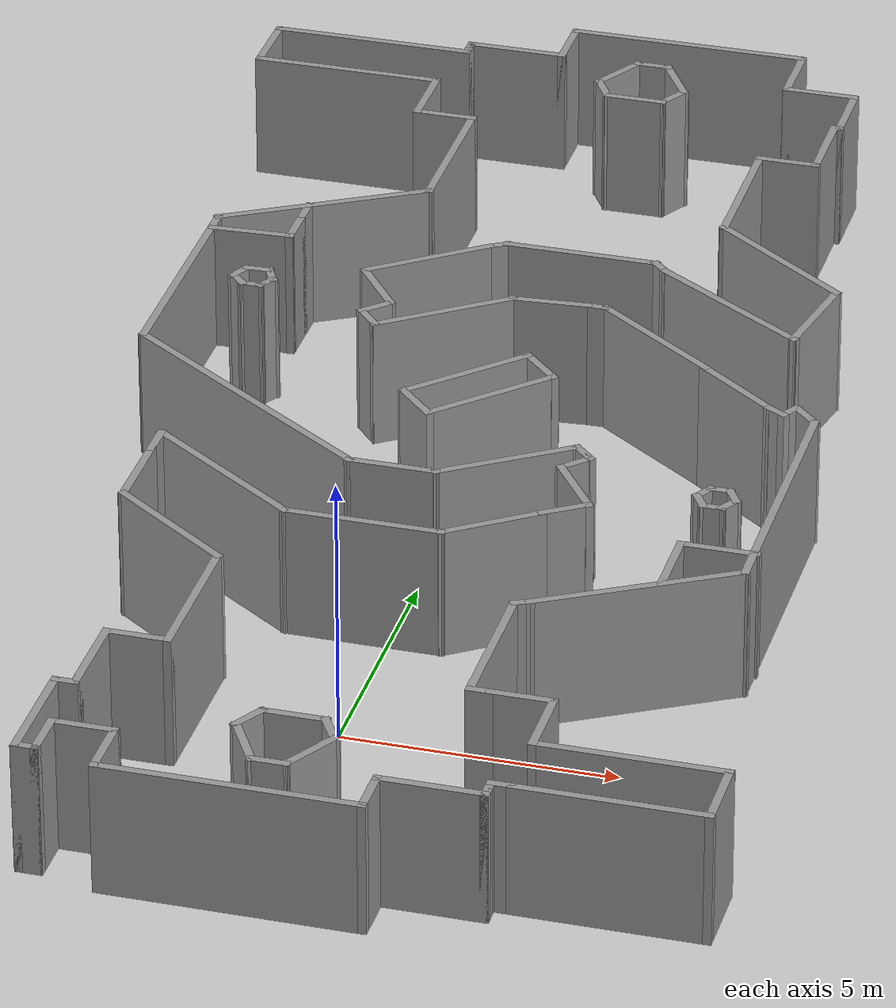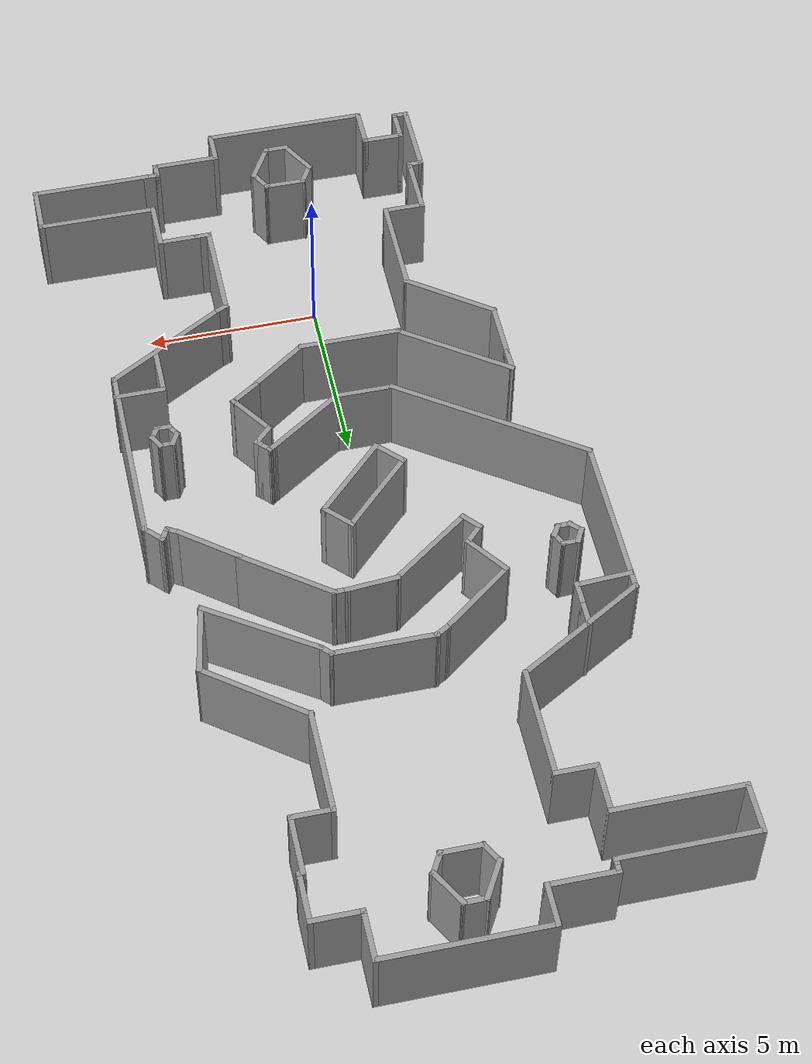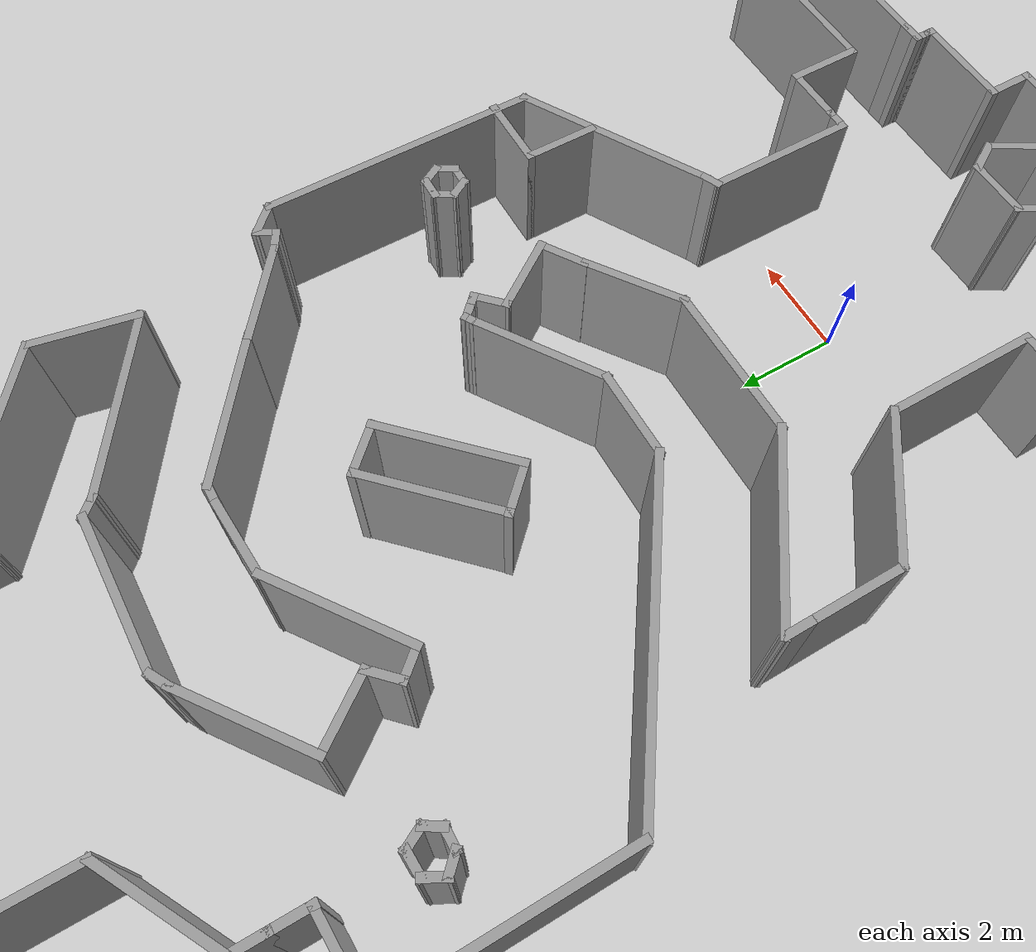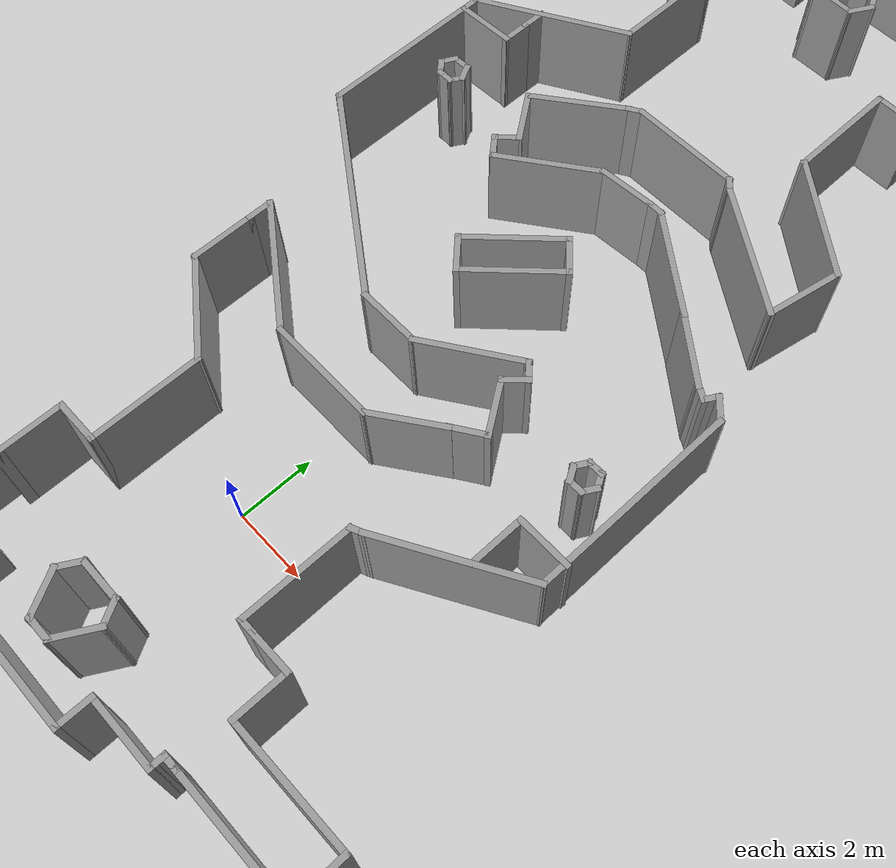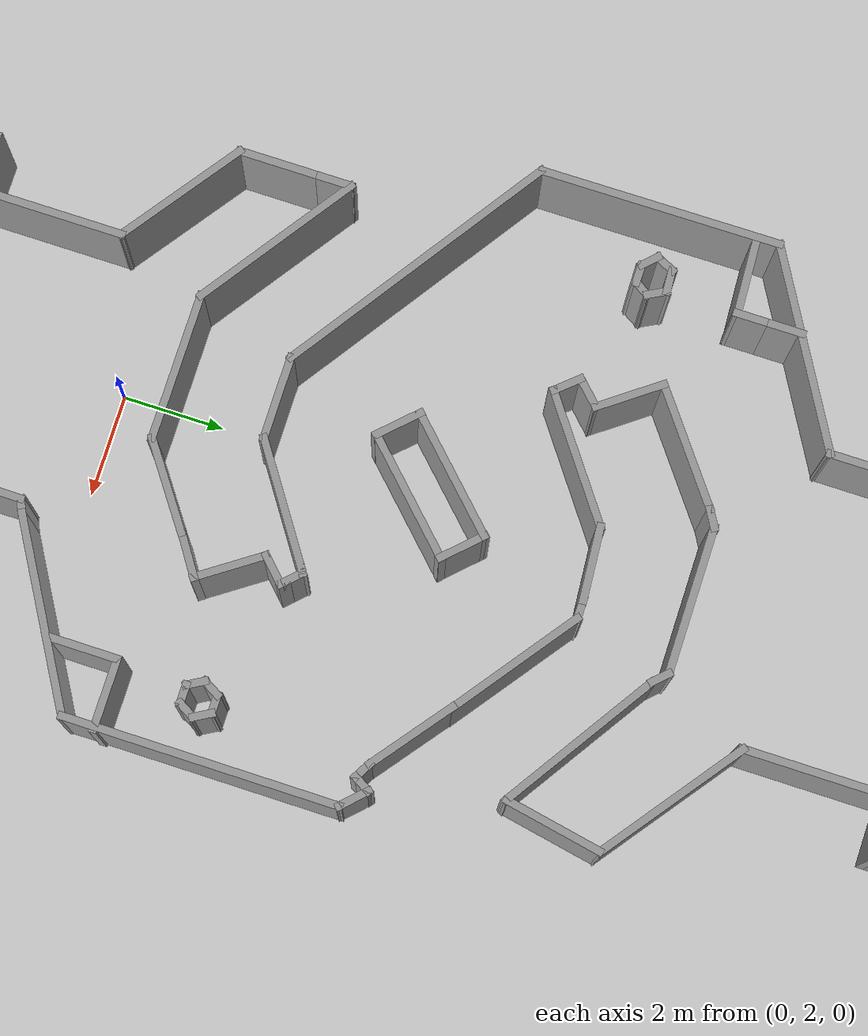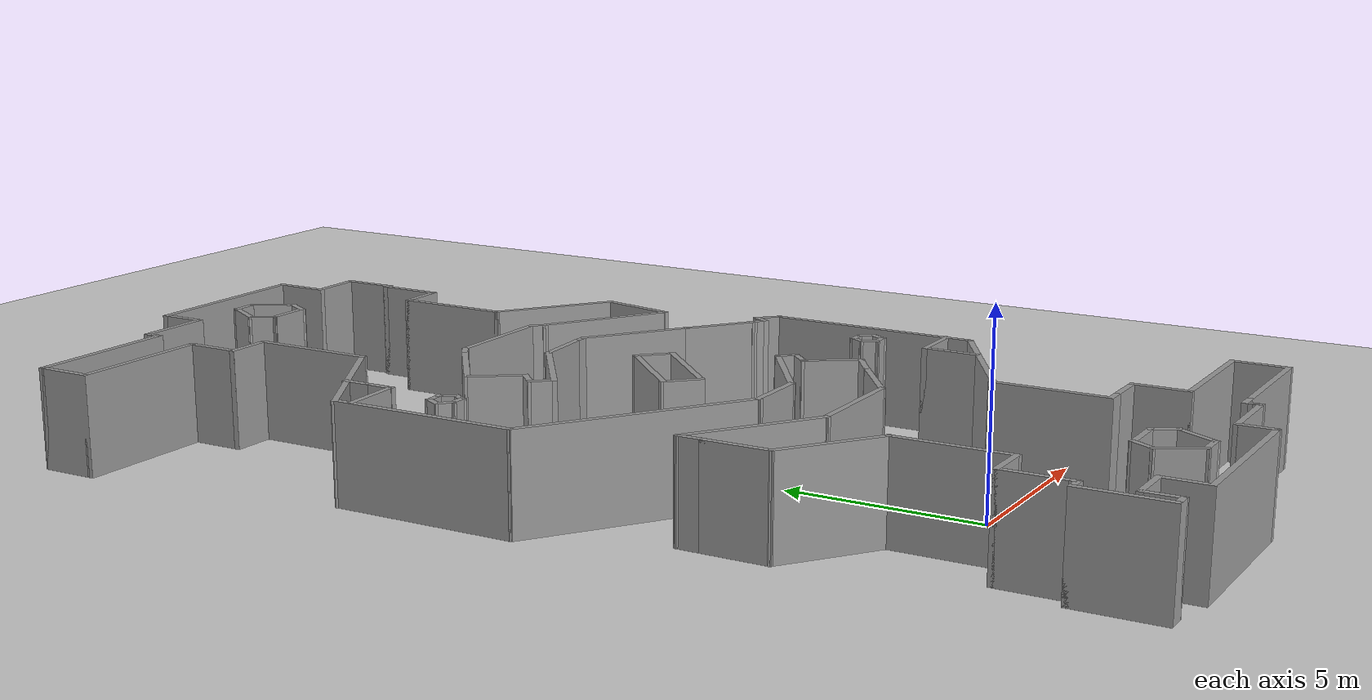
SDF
<sdf version="1.7">
 <world name="default">
  <light name="sun" type="directional">
   <pose>0 0 10 0 -0 0</pose>
   <diffuse>0.8 0.8 0.8 1</diffuse>
   <specular>0.2 0.2 0.2 1</specular>
   <attenuation>
    <range>1000</range>
    <constant>0.9</constant>
    <linear>0.01</linear>
    <quadratic>0.001</quadratic>
   </attenuation>
   <direction>-0.5 0.1 -0.9</direction>
   <spot><inner_angle>0</inner_angle><outer_angle>0</outer_angle><falloff>0</falloff></spot>
  </light>
  <model name="ground_plane">
   <static>1</static>
   <link name="link">
    <collision name="collision">
     <geometry><plane><normal>0 0 1</normal><size>100 100</size></plane></geometry>
     <surface>
      <contact><collide_bitmask>65535</collide_bitmask></contact>
      <friction><ode><mu>100</mu><mu2>50</mu2></ode></friction>
     </surface>
    </collision>
    <visual name="visual">
     <cast_shadows>0</cast_shadows>
     <geometry><plane><normal>0 0 1</normal><size>100 100</size></plane></geometry>
     <material>
      <script><uri>file://media/materials/scripts/gazebo.material</uri><name>Gazebo/Grey</name></script>
     </material>
    </visual>
   </link>
  </model>
  <gravity>0 0 -9.8</gravity>
  <magnetic_field>6e-06 2.3e-05 -4.2e-05</magnetic_field>
  <atmosphere type="adiabatic"/>
  <physics type="ode">
   <max_step_size>0.001</max_step_size>
   <real_time_factor>1</real_time_factor>
   <real_time_update_rate>1000</real_time_update_rate>
  </physics>
  <scene><ambient>0.4 0.4 0.4 1</ambient><background>0.7 0.7 0.7 1</background><shadows>1</shadows></scene>
  <spherical_coordinates>
   <surface_model>EARTH_WGS84</surface_model>
   <latitude_deg>0</latitude_deg>
   <longitude_deg>0</longitude_deg>
   <elevation>0</elevation>
   <heading_deg>0</heading_deg>
  </spherical_coordinates>
  <model name="all_changdi">
   <pose>0.143338 8.39111 0 0 0 -1.57051</pose>
   <link name="Wall_0">
    <collision name="Wall_0_Collision">
     <geometry><box><size>3.05417 0.15 2.5</size></box></geometry>
     <pose>0 0 1.25 0 -0 0</pose>
    </collision>
    <visual name="Wall_0_Visual">
     <pose>0 0 1.25 0 -0 0</pose>
     <geometry><box><size>3.05417 0.15 2.5</size></box></geometry>
     <material>
      <script><uri>file://media/materials/scripts/gazebo.material</uri><name>Gazebo/Grey</name></script>
      <ambient>1 1 1 1</ambient>
     </material>
     <meta><layer>0</layer></meta>
    </visual>
    <pose>-8.26691 2.98126 0 0 -0 0</pose>
   </link>
   <link name="Wall_10">
    <collision name="Wall_10_Collision">
     <geometry><box><size>2 0.15 2.5</size></box></geometry>
     <pose>0 0 1.25 0 -0 0</pose>
    </collision>
    <visual name="Wall_10_Visual">
     <pose>0 0 1.25 0 -0 0</pose>
     <geometry><box><size>2 0.15 2.5</size></box></geometry>
     <material>
      <script><uri>file://media/materials/scripts/gazebo.material</uri><name>Gazebo/Grey</name></script>
      <ambient>1 1 1 1</ambient>
     </material>
     <meta><layer>0</layer></meta>
    </visual>
    <pose>-12.919 -2.69374 0 0 -0 -1.5708</pose>
   </link>
   <link name="Wall_100">
    <collision name="Wall_100_Collision">
     <geometry><box><size>1.75 0.15 2.5</size></box></geometry>
     <pose>0 0 1.25 0 -0 0</pose>
    </collision>
    <visual name="Wall_100_Visual">
     <pose>0 0 1.25 0 -0 0</pose>
     <geometry><box><size>1.75 0.15 2.5</size></box></geometry>
     <material>
      <script><uri>file://media/materials/scripts/gazebo.material</uri><name>Gazebo/Grey</name></script>
      <ambient>1 1 1 1</ambient>
     </material>
     <meta><layer>0</layer></meta>
    </visual>
    <pose>4.70961 -4.90602 0 0 -0 0</pose>
   </link>
   <link name="Wall_101">
    <collision name="Wall_101_Collision">
     <geometry><box><size>2.89585 0.15 2.5</size></box></geometry>
     <pose>0 0 1.25 0 -0 0</pose>
    </collision>
    <visual name="Wall_101_Visual">
     <pose>0 0 1.25 0 -0 0</pose>
     <geometry><box><size>2.89585 0.15 2.5</size></box></geometry>
     <material>
      <script><uri>file://media/materials/scripts/gazebo.material</uri><name>Gazebo/Grey</name></script>
      <ambient>1 1 1 1</ambient>
     </material>
     <meta><layer>0</layer></meta>
    </visual>
    <pose>6.3143 -3.79364 0 0 -0 0.94454</pose>
   </link>
   <link name="Wall_104">
    <collision name="Wall_104_Collision">
     <geometry><box><size>3 0.15 2.5</size></box></geometry>
     <pose>0 0 1.25 0 -0 0</pose>
    </collision>
    <visual name="Wall_104_Visual">
     <pose>0 0 1.25 0 -0 0</pose>
     <geometry><box><size>3 0.15 2.5</size></box></geometry>
     <material>
      <script><uri>file://media/materials/scripts/gazebo.material</uri><name>Gazebo/Grey</name></script>
      <ambient>1 1 1 1</ambient>
     </material>
     <meta><layer>0</layer></meta>
    </visual>
    <pose>8.544 -2.68126 0 0 -0 0</pose>
   </link>
   <link name="Wall_105">
    <collision name="Wall_105_Collision">
     <geometry><box><size>1.25 0.15 2.5</size></box></geometry>
     <pose>0 0 1.25 0 -0 0</pose>
    </collision>
    <visual name="Wall_105_Visual">
     <pose>0 0 1.25 0 -0 0</pose>
     <geometry><box><size>1.25 0.15 2.5</size></box></geometry>
     <material>
      <script><uri>file://media/materials/scripts/gazebo.material</uri><name>Gazebo/Grey</name></script>
      <ambient>1 1 1 1</ambient>
     </material>
     <meta><layer>0</layer></meta>
    </visual>
    <pose>9.96899 -3.23126 0 0 -0 -1.5708</pose>
   </link>
   <link name="Wall_106">
    <collision name="Wall_106_Collision">
     <geometry><box><size>1.75 0.15 2.5</size></box></geometry>
     <pose>0 0 1.25 0 -0 0</pose>
    </collision>
    <visual name="Wall_106_Visual">
     <pose>0 0 1.25 0 -0 0</pose>
     <geometry><box><size>1.75 0.15 2.5</size></box></geometry>
     <material>
      <script><uri>file://media/materials/scripts/gazebo.material</uri><name>Gazebo/Grey</name></script>
      <ambient>1 1 1 1</ambient>
     </material>
     <meta><layer>0</layer></meta>
    </visual>
    <pose>10.769 -3.78126 0 0 -0 0</pose>
   </link>
   <link name="Wall_107">
    <collision name="Wall_107_Collision">
     <geometry><box><size>0.25 0.15 2.5</size></box></geometry>
     <pose>0 0 1.25 0 -0 0</pose>
    </collision>
    <visual name="Wall_107_Visual">
     <pose>0 0 1.25 0 -0 0</pose>
     <geometry><box><size>0.25 0.15 2.5</size></box></geometry>
     <material>
      <script><uri>file://media/materials/scripts/gazebo.material</uri><name>Gazebo/Grey</name></script>
      <ambient>1 1 1 1</ambient>
     </material>
     <meta><layer>0</layer></meta>
    </visual>
    <pose>11.619 -3.78126 0 0 -0 0</pose>
   </link>
   <link name="Wall_108">
    <collision name="Wall_108_Collision">
     <geometry><box><size>0.5 0.15 2.5</size></box></geometry>
     <pose>0 0 1.25 0 -0 0</pose>
    </collision>
    <visual name="Wall_108_Visual">
     <pose>0 0 1.25 0 -0 0</pose>
     <geometry><box><size>0.5 0.15 2.5</size></box></geometry>
     <material>
      <script><uri>file://media/materials/scripts/gazebo.material</uri><name>Gazebo/Grey</name></script>
      <ambient>1 1 1 1</ambient>
     </material>
     <meta><layer>0</layer></meta>
    </visual>
    <pose>11.669 -3.95626 0 0 -0 -1.5708</pose>
   </link>
   <link name="Wall_109">
    <collision name="Wall_109_Collision">
     <geometry><box><size>2.25 0.15 2.5</size></box></geometry>
     <pose>0 0 1.25 0 -0 0</pose>
    </collision>
    <visual name="Wall_109_Visual">
     <pose>0 0 1.25 0 -0 0</pose>
     <geometry><box><size>2.25 0.15 2.5</size></box></geometry>
     <material>
      <script><uri>file://media/materials/scripts/gazebo.material</uri><name>Gazebo/Grey</name></script>
      <ambient>1 1 1 1</ambient>
     </material>
     <meta><layer>0</layer></meta>
    </visual>
    <pose>12.719 -4.13126 0 0 -0 0</pose>
   </link>
   <link name="Wall_11">
    <collision name="Wall_11_Collision">
     <geometry><box><size>0.25 0.15 2.5</size></box></geometry>
     <pose>0 0 1.25 0 -0 0</pose>
    </collision>
    <visual name="Wall_11_Visual">
     <pose>0 0 1.25 0 -0 0</pose>
     <geometry><box><size>0.25 0.15 2.5</size></box></geometry>
     <material>
      <script><uri>file://media/materials/scripts/gazebo.material</uri><name>Gazebo/Grey</name></script>
      <ambient>1 1 1 1</ambient>
     </material>
     <meta><layer>0</layer></meta>
    </visual>
    <pose>-12.869 -3.61874 0 0 -0 0</pose>
   </link>
   <link name="Wall_110">
    <collision name="Wall_110_Collision">
     <geometry><box><size>0.5 0.15 2.5</size></box></geometry>
     <pose>0 0 1.25 0 -0 0</pose>
    </collision>
    <visual name="Wall_110_Visual">
     <pose>0 0 1.25 0 -0 0</pose>
     <geometry><box><size>0.5 0.15 2.5</size></box></geometry>
     <material>
      <script><uri>file://media/materials/scripts/gazebo.material</uri><name>Gazebo/Grey</name></script>
      <ambient>1 1 1 1</ambient>
     </material>
     <meta><layer>0</layer></meta>
    </visual>
    <pose>13.769 -3.95626 0 0 -0 1.5708</pose>
   </link>
   <link name="Wall_111">
    <collision name="Wall_111_Collision">
     <geometry><box><size>1 0.15 2.5</size></box></geometry>
     <pose>0 0 1.25 0 -0 0</pose>
    </collision>
    <visual name="Wall_111_Visual">
     <pose>0 0 1.25 0 -0 0</pose>
     <geometry><box><size>1 0.15 2.5</size></box></geometry>
     <material>
      <script><uri>file://media/materials/scripts/gazebo.material</uri><name>Gazebo/Grey</name></script>
      <ambient>1 1 1 1</ambient>
     </material>
     <meta><layer>0</layer></meta>
    </visual>
    <pose>13.344 -3.78126 0 0 -0 3.14159</pose>
   </link>
   <link name="Wall_112">
    <collision name="Wall_112_Collision">
     <geometry><box><size>1.25 0.15 2.5</size></box></geometry>
     <pose>0 0 1.25 0 -0 0</pose>
    </collision>
    <visual name="Wall_112_Visual">
     <pose>0 0 1.25 0 -0 0</pose>
     <geometry><box><size>1.25 0.15 2.5</size></box></geometry>
     <material>
      <script><uri>file://media/materials/scripts/gazebo.material</uri><name>Gazebo/Grey</name></script>
      <ambient>1 1 1 1</ambient>
     </material>
     <meta><layer>0</layer></meta>
    </visual>
    <pose>12.919 -3.23126 0 0 -0 1.5708</pose>
   </link>
   <link name="Wall_113">
    <collision name="Wall_113_Collision">
     <geometry><box><size>1.25 0.15 2.5</size></box></geometry>
     <pose>0 0 1.25 0 -0 0</pose>
    </collision>
    <visual name="Wall_113_Visual">
     <pose>0 0 1.25 0 -0 0</pose>
     <geometry><box><size>1.25 0.15 2.5</size></box></geometry>
     <material>
      <script><uri>file://media/materials/scripts/gazebo.material</uri><name>Gazebo/Grey</name></script>
      <ambient>1 1 1 1</ambient>
     </material>
     <meta><layer>0</layer></meta>
    </visual>
    <pose>13.469 -2.68126 0 0 -0 0</pose>
   </link>
   <link name="Wall_115">
    <collision name="Wall_115_Collision">
     <geometry><box><size>4.75 0.15 2.5</size></box></geometry>
     <pose>0 0 1.25 0 -0 0</pose>
    </collision>
    <visual name="Wall_115_Visual">
     <pose>0 0 1.25 0 -0 0</pose>
     <geometry><box><size>4.75 0.15 2.5</size></box></geometry>
     <material>
      <script><uri>file://media/materials/scripts/gazebo.material</uri><name>Gazebo/Grey</name></script>
      <ambient>1 1 1 1</ambient>
     </material>
     <meta><layer>0</layer></meta>
    </visual>
    <pose>14.019 -0.381256 0 0 -0 1.5708</pose>
   </link>
   <link name="Wall_116">
    <collision name="Wall_116_Collision">
     <geometry><box><size>1 0.15 2.5</size></box></geometry>
     <pose>0 0 1.25 0 -0 0</pose>
    </collision>
    <visual name="Wall_116_Visual">
     <pose>0 0 1.25 0 -0 0</pose>
     <geometry><box><size>1 0.15 2.5</size></box></geometry>
     <material>
      <script><uri>file://media/materials/scripts/gazebo.material</uri><name>Gazebo/Grey</name></script>
      <ambient>1 1 1 1</ambient>
     </material>
     <meta><layer>0</layer></meta>
    </visual>
    <pose>13.594 1.91874 0 0 -0 3.14159</pose>
   </link>
   <link name="Wall_118">
    <collision name="Wall_118_Collision">
     <geometry><box><size>2 0.15 2.5</size></box></geometry>
     <pose>0 0 1.25 0 -0 0</pose>
    </collision>
    <visual name="Wall_118_Visual">
     <pose>0 0 1.25 0 -0 0</pose>
     <geometry><box><size>2 0.15 2.5</size></box></geometry>
     <material>
      <script><uri>file://media/materials/scripts/gazebo.material</uri><name>Gazebo/Grey</name></script>
      <ambient>1 1 1 1</ambient>
     </material>
     <meta><layer>0</layer></meta>
    </visual>
    <pose>13.169 2.84374 0 0 -0 1.5708</pose>
   </link>
   <link name="Wall_119">
    <collision name="Wall_119_Collision">
     <geometry><box><size>0.25 0.15 2.5</size></box></geometry>
     <pose>0 0 1.25 0 -0 0</pose>
    </collision>
    <visual name="Wall_119_Visual">
     <pose>0 0 1.25 0 -0 0</pose>
     <geometry><box><size>0.25 0.15 2.5</size></box></geometry>
     <material>
      <script><uri>file://media/materials/scripts/gazebo.material</uri><name>Gazebo/Grey</name></script>
      <ambient>1 1 1 1</ambient>
     </material>
     <meta><layer>0</layer></meta>
    </visual>
    <pose>13.119 3.76874 0 0 -0 3.14159</pose>
   </link>
   <link name="Wall_121">
    <collision name="Wall_121_Collision">
     <geometry><box><size>0.5 0.15 2.5</size></box></geometry>
     <pose>0 0 1.25 0 -0 0</pose>
    </collision>
    <visual name="Wall_121_Visual">
     <pose>0 0 1.25 0 -0 0</pose>
     <geometry><box><size>0.5 0.15 2.5</size></box></geometry>
     <material>
      <script><uri>file://media/materials/scripts/gazebo.material</uri><name>Gazebo/Grey</name></script>
      <ambient>1 1 1 1</ambient>
     </material>
     <meta><layer>0</layer></meta>
    </visual>
    <pose>12.994 3.76874 0 0 -0 3.14159</pose>
   </link>
   <link name="Wall_122">
    <collision name="Wall_122_Collision">
     <geometry><box><size>0.5 0.15 2.5</size></box></geometry>
     <pose>0 0 1.25 0 -0 0</pose>
    </collision>
    <visual name="Wall_122_Visual">
     <pose>0 0 1.25 0 -0 0</pose>
     <geometry><box><size>0.5 0.15 2.5</size></box></geometry>
     <material>
      <script><uri>file://media/materials/scripts/gazebo.material</uri><name>Gazebo/Grey</name></script>
      <ambient>1 1 1 1</ambient>
     </material>
     <meta><layer>0</layer></meta>
    </visual>
    <pose>12.819 3.94374 0 0 -0 1.5708</pose>
   </link>
   <link name="Wall_123">
    <collision name="Wall_123_Collision">
     <geometry><box><size>3.5 0.15 2.5</size></box></geometry>
     <pose>0 0 1.25 0 -0 0</pose>
    </collision>
    <visual name="Wall_123_Visual">
     <pose>0 0 1.25 0 -0 0</pose>
     <geometry><box><size>3.5 0.15 2.5</size></box></geometry>
     <material>
      <script><uri>file://media/materials/scripts/gazebo.material</uri><name>Gazebo/Grey</name></script>
      <ambient>1 1 1 1</ambient>
     </material>
     <meta><layer>0</layer></meta>
    </visual>
    <pose>12.819 5.79374 0 0 -0 1.5708</pose>
   </link>
   <link name="Wall_124">
    <collision name="Wall_124_Collision">
     <geometry><box><size>1.5 0.15 2.5</size></box></geometry>
     <pose>0 0 1.25 0 -0 0</pose>
    </collision>
    <visual name="Wall_124_Visual">
     <pose>0 0 1.25 0 -0 0</pose>
     <geometry><box><size>1.5 0.15 2.5</size></box></geometry>
     <material>
      <script><uri>file://media/materials/scripts/gazebo.material</uri><name>Gazebo/Grey</name></script>
      <ambient>1 1 1 1</ambient>
     </material>
     <meta><layer>0</layer></meta>
    </visual>
    <pose>12.144 7.46874 0 0 -0 3.14159</pose>
   </link>
   <link name="Wall_125">
    <collision name="Wall_125_Collision">
     <geometry><box><size>3.5 0.15 2.5</size></box></geometry>
     <pose>0 0 1.25 0 -0 0</pose>
    </collision>
    <visual name="Wall_125_Visual">
     <pose>0 0 1.25 0 -0 0</pose>
     <geometry><box><size>3.5 0.15 2.5</size></box></geometry>
     <material>
      <script><uri>file://media/materials/scripts/gazebo.material</uri><name>Gazebo/Grey</name></script>
      <ambient>1 1 1 1</ambient>
     </material>
     <meta><layer>0</layer></meta>
    </visual>
    <pose>11.469 5.79374 0 0 -0 -1.5708</pose>
   </link>
   <link name="Wall_126">
    <collision name="Wall_126_Collision">
     <geometry><box><size>1.5 0.15 2.5</size></box></geometry>
     <pose>0 0 1.25 0 -0 0</pose>
    </collision>
    <visual name="Wall_126_Visual">
     <pose>0 0 1.25 0 -0 0</pose>
     <geometry><box><size>1.5 0.15 2.5</size></box></geometry>
     <material>
      <script><uri>file://media/materials/scripts/gazebo.material</uri><name>Gazebo/Grey</name></script>
      <ambient>1 1 1 1</ambient>
     </material>
     <meta><layer>0</layer></meta>
    </visual>
    <pose>10.794 4.11874 0 0 -0 3.14159</pose>
   </link>
   <link name="Wall_127">
    <collision name="Wall_127_Collision">
     <geometry><box><size>1.25 0.15 2.5</size></box></geometry>
     <pose>0 0 1.25 0 -0 0</pose>
    </collision>
    <visual name="Wall_127_Visual">
     <pose>0 0 1.25 0 -0 0</pose>
     <geometry><box><size>1.25 0.15 2.5</size></box></geometry>
     <material>
      <script><uri>file://media/materials/scripts/gazebo.material</uri><name>Gazebo/Grey</name></script>
      <ambient>1 1 1 1</ambient>
     </material>
     <meta><layer>0</layer></meta>
    </visual>
    <pose>10.119 3.56874 0 0 -0 -1.5708</pose>
   </link>
   <link name="Wall_128">
    <collision name="Wall_128_Collision">
     <geometry><box><size>0.5 0.15 2.5</size></box></geometry>
     <pose>0 0 1.25 0 -0 0</pose>
    </collision>
    <visual name="Wall_128_Visual">
     <pose>0 0 1.25 0 -0 0</pose>
     <geometry><box><size>0.5 0.15 2.5</size></box></geometry>
     <material>
      <script><uri>file://media/materials/scripts/gazebo.material</uri><name>Gazebo/Grey</name></script>
      <ambient>1 1 1 1</ambient>
     </material>
     <meta><layer>0</layer></meta>
    </visual>
    <pose>10.119 2.84374 0 0 -0 -1.5708</pose>
   </link>
   <link name="Wall_129">
    <collision name="Wall_129_Collision">
     <geometry><box><size>3 0.15 2.5</size></box></geometry>
     <pose>0 0 1.25 0 -0 0</pose>
    </collision>
    <visual name="Wall_129_Visual">
     <pose>0 0 1.25 0 -0 0</pose>
     <geometry><box><size>3 0.15 2.5</size></box></geometry>
     <material>
      <script><uri>file://media/materials/scripts/gazebo.material</uri><name>Gazebo/Grey</name></script>
      <ambient>1 1 1 1</ambient>
     </material>
     <meta><layer>0</layer></meta>
    </visual>
    <pose>8.69399 2.66874 0 0 -0 3.14159</pose>
   </link>
   <link name="Wall_13">
    <collision name="Wall_13_Collision">
     <geometry><box><size>0.5 0.15 2.5</size></box></geometry>
     <pose>0 0 1.25 0 -0 0</pose>
    </collision>
    <visual name="Wall_13_Visual">
     <pose>0 0 1.25 0 -0 0</pose>
     <geometry><box><size>0.5 0.15 2.5</size></box></geometry>
     <material>
      <script><uri>file://media/materials/scripts/gazebo.material</uri><name>Gazebo/Grey</name></script>
      <ambient>1 1 1 1</ambient>
     </material>
     <meta><layer>0</layer></meta>
    </visual>
    <pose>-12.744 -3.61874 0 0 -0 0</pose>
   </link>
   <link name="Wall_130">
    <collision name="Wall_130_Collision">
     <geometry><box><size>0.420828 0.15 2.5</size></box></geometry>
     <pose>0 0 1.25 0 -0 0</pose>
    </collision>
    <visual name="Wall_130_Visual">
     <pose>0 0 1.25 0 -0 0</pose>
     <geometry><box><size>0.420828 0.15 2.5</size></box></geometry>
     <material>
      <script><uri>file://media/materials/scripts/gazebo.material</uri><name>Gazebo/Grey</name></script>
      <ambient>1 1 1 1</ambient>
     </material>
     <meta><layer>0</layer></meta>
    </visual>
    <pose>7.21367 2.79234 0 0 -0 1.99164</pose>
   </link>
   <link name="Wall_132">
    <collision name="Wall_132_Collision">
     <geometry><box><size>0.526214 0.15 2.5</size></box></geometry>
     <pose>0 0 1.25 0 -0 0</pose>
    </collision>
    <visual name="Wall_132_Visual">
     <pose>0 0 1.25 0 -0 0</pose>
     <geometry><box><size>0.526214 0.15 2.5</size></box></geometry>
     <material>
      <script><uri>file://media/materials/scripts/gazebo.material</uri><name>Gazebo/Grey</name></script>
      <ambient>1 1 1 1</ambient>
     </material>
     <meta><layer>0</layer></meta>
    </visual>
    <pose>-2.80129 -4.70495 0 0 -0 0.483817</pose>
   </link>
   <link name="Wall_133">
    <collision name="Wall_133_Collision">
     <geometry><box><size>0.461748 0.15 2.5</size></box></geometry>
     <pose>0 0 1.25 0 -0 0</pose>
    </collision>
    <visual name="Wall_133_Visual">
     <pose>0 0 1.25 0 -0 0</pose>
     <geometry><box><size>0.461748 0.15 2.5</size></box></geometry>
     <material>
      <script><uri>file://media/materials/scripts/gazebo.material</uri><name>Gazebo/Grey</name></script>
      <ambient>1 1 1 1</ambient>
     </material>
     <meta><layer>0</layer></meta>
    </visual>
    <pose>-2.5015 -4.6983 0 0 -0 -0.545315</pose>
   </link>
   <link name="Wall_134">
    <collision name="Wall_134_Collision">
     <geometry><box><size>0.5 0.15 2.5</size></box></geometry>
     <pose>0 0 1.25 0 -0 0</pose>
    </collision>
    <visual name="Wall_134_Visual">
     <pose>0 0 1.25 0 -0 0</pose>
     <geometry><box><size>0.5 0.15 2.5</size></box></geometry>
     <material>
      <script><uri>file://media/materials/scripts/gazebo.material</uri><name>Gazebo/Grey</name></script>
      <ambient>1 1 1 1</ambient>
     </material>
     <meta><layer>0</layer></meta>
    </visual>
    <pose>-2.36824 -4.95415 0 0 -0 -1.5708</pose>
   </link>
   <link name="Wall_135">
    <collision name="Wall_135_Collision">
     <geometry><box><size>0.5 0.15 2.5</size></box></geometry>
     <pose>0 0 1.25 0 -0 0</pose>
    </collision>
    <visual name="Wall_135_Visual">
     <pose>0 0 1.25 0 -0 0</pose>
     <geometry><box><size>0.5 0.15 2.5</size></box></geometry>
     <material>
      <script><uri>file://media/materials/scripts/gazebo.material</uri><name>Gazebo/Grey</name></script>
      <ambient>1 1 1 1</ambient>
     </material>
     <meta><layer>0</layer></meta>
    </visual>
    <pose>-2.49198 -5.2529 0 0 -0 -2.35619</pose>
   </link>
   <link name="Wall_136">
    <collision name="Wall_136_Collision">
     <geometry><box><size>0.526214 0.15 2.5</size></box></geometry>
     <pose>0 0 1.25 0 -0 0</pose>
    </collision>
    <visual name="Wall_136_Visual">
     <pose>0 0 1.25 0 -0 0</pose>
     <geometry><box><size>0.526214 0.15 2.5</size></box></geometry>
     <material>
      <script><uri>file://media/materials/scripts/gazebo.material</uri><name>Gazebo/Grey</name></script>
      <ambient>1 1 1 1</ambient>
     </material>
     <meta><layer>0</layer></meta>
    </visual>
    <pose>-2.78224 -5.28914 0 0 -0 2.65778</pose>
   </link>
   <link name="Wall_137">
    <collision name="Wall_137_Collision">
     <geometry><box><size>0.559798 0.15 2.5</size></box></geometry>
     <pose>0 0 1.25 0 -0 0</pose>
    </collision>
    <visual name="Wall_137_Visual">
     <pose>0 0 1.25 0 -0 0</pose>
     <geometry><box><size>0.559798 0.15 2.5</size></box></geometry>
     <material>
      <script><uri>file://media/materials/scripts/gazebo.material</uri><name>Gazebo/Grey</name></script>
      <ambient>1 1 1 1</ambient>
     </material>
     <meta><layer>0</layer></meta>
    </visual>
    <pose>-2.95662 -4.99705 0 0 -0 1.62541</pose>
   </link>
   <link name="Wall_139">
    <collision name="Wall_139_Collision">
     <geometry><box><size>0.5 0.15 2.5</size></box></geometry>
     <pose>0 0 1.25 0 -0 0</pose>
    </collision>
    <visual name="Wall_139_Visual">
     <pose>0 0 1.25 0 -0 0</pose>
     <geometry><box><size>0.5 0.15 2.5</size></box></geometry>
     <material>
      <script><uri>file://media/materials/scripts/gazebo.material</uri><name>Gazebo/Grey</name></script>
      <ambient>1 1 1 1</ambient>
     </material>
     <meta><layer>0</layer></meta>
    </visual>
    <pose>2.63396 5.18389 0 0 -0 -1.5708</pose>
   </link>
   <link name="Wall_140">
    <collision name="Wall_140_Collision">
     <geometry><box><size>0.5 0.15 2.5</size></box></geometry>
     <pose>0 0 1.25 0 -0 0</pose>
    </collision>
    <visual name="Wall_140_Visual">
     <pose>0 0 1.25 0 -0 0</pose>
     <geometry><box><size>0.5 0.15 2.5</size></box></geometry>
     <material>
      <script><uri>file://media/materials/scripts/gazebo.material</uri><name>Gazebo/Grey</name></script>
      <ambient>1 1 1 1</ambient>
     </material>
     <meta><layer>0</layer></meta>
    </visual>
    <pose>2.78551 4.92139 0 0 -0 -0.523599</pose>
   </link>
   <link name="Wall_141">
    <collision name="Wall_141_Collision">
     <geometry><box><size>0.5 0.15 2.5</size></box></geometry>
     <pose>0 0 1.25 0 -0 0</pose>
    </collision>
    <visual name="Wall_141_Visual">
     <pose>0 0 1.25 0 -0 0</pose>
     <geometry><box><size>0.5 0.15 2.5</size></box></geometry>
     <material>
      <script><uri>file://media/materials/scripts/gazebo.material</uri><name>Gazebo/Grey</name></script>
      <ambient>1 1 1 1</ambient>
     </material>
     <meta><layer>0</layer></meta>
    </visual>
    <pose>3.08862 4.92139 0 0 -0 0.523599</pose>
   </link>
   <link name="Wall_142">
    <collision name="Wall_142_Collision">
     <geometry><box><size>0.5 0.15 2.5</size></box></geometry>
     <pose>0 0 1.25 0 -0 0</pose>
    </collision>
    <visual name="Wall_142_Visual">
     <pose>0 0 1.25 0 -0 0</pose>
     <geometry><box><size>0.5 0.15 2.5</size></box></geometry>
     <material>
      <script><uri>file://media/materials/scripts/gazebo.material</uri><name>Gazebo/Grey</name></script>
      <ambient>1 1 1 1</ambient>
     </material>
     <meta><layer>0</layer></meta>
    </visual>
    <pose>3.24017 5.18389 0 0 -0 1.5708</pose>
   </link>
   <link name="Wall_143">
    <collision name="Wall_143_Collision">
     <geometry><box><size>0.5 0.15 2.5</size></box></geometry>
     <pose>0 0 1.25 0 -0 0</pose>
    </collision>
    <visual name="Wall_143_Visual">
     <pose>0 0 1.25 0 -0 0</pose>
     <geometry><box><size>0.5 0.15 2.5</size></box></geometry>
     <material>
      <script><uri>file://media/materials/scripts/gazebo.material</uri><name>Gazebo/Grey</name></script>
      <ambient>1 1 1 1</ambient>
     </material>
     <meta><layer>0</layer></meta>
    </visual>
    <pose>3.08862 5.44639 0 0 -0 2.61799</pose>
   </link>
   <link name="Wall_144">
    <collision name="Wall_144_Collision">
     <geometry><box><size>0.5 0.15 2.5</size></box></geometry>
     <pose>0 0 1.25 0 -0 0</pose>
    </collision>
    <visual name="Wall_144_Visual">
     <pose>0 0 1.25 0 -0 0</pose>
     <geometry><box><size>0.5 0.15 2.5</size></box></geometry>
     <material>
      <script><uri>file://media/materials/scripts/gazebo.material</uri><name>Gazebo/Grey</name></script>
      <ambient>1 1 1 1</ambient>
     </material>
     <meta><layer>0</layer></meta>
    </visual>
    <pose>2.78551 5.44639 0 0 -0 -2.61799</pose>
   </link>
   <link name="Wall_146">
    <collision name="Wall_146_Collision">
     <geometry><box><size>0.75 0.15 2.5</size></box></geometry>
     <pose>0 0 1.25 0 -0 0</pose>
    </collision>
    <visual name="Wall_146_Visual">
     <pose>0 0 1.25 0 -0 0</pose>
     <geometry><box><size>0.75 0.15 2.5</size></box></geometry>
     <material>
      <script><uri>file://media/materials/scripts/gazebo.material</uri><name>Gazebo/Grey</name></script>
      <ambient>1 1 1 1</ambient>
     </material>
     <meta><layer>0</layer></meta>
    </visual>
    <pose>11.9405 0.758184 0 0 -0 -2.61799</pose>
   </link>
   <link name="Wall_147">
    <collision name="Wall_147_Collision">
     <geometry><box><size>1.25 0.15 2.5</size></box></geometry>
     <pose>0 0 1.25 0 -0 0</pose>
    </collision>
    <visual name="Wall_147_Visual">
     <pose>0 0 1.25 0 -0 0</pose>
     <geometry><box><size>1.25 0.15 2.5</size></box></geometry>
     <material>
      <script><uri>file://media/materials/scripts/gazebo.material</uri><name>Gazebo/Grey</name></script>
      <ambient>1 1 1 1</ambient>
     </material>
     <meta><layer>0</layer></meta>
    </visual>
    <pose>11.6807 0.058184 0 0 -0 -1.5708</pose>
   </link>
   <link name="Wall_148">
    <collision name="Wall_148_Collision">
     <geometry><box><size>0.75 0.15 2.5</size></box></geometry>
     <pose>0 0 1.25 0 -0 0</pose>
    </collision>
    <visual name="Wall_148_Visual">
     <pose>0 0 1.25 0 -0 0</pose>
     <geometry><box><size>0.75 0.15 2.5</size></box></geometry>
     <material>
      <script><uri>file://media/materials/scripts/gazebo.material</uri><name>Gazebo/Grey</name></script>
      <ambient>1 1 1 1</ambient>
     </material>
     <meta><layer>0</layer></meta>
    </visual>
    <pose>11.9405 -0.641816 0 0 -0 -0.523599</pose>
   </link>
   <link name="Wall_149">
    <collision name="Wall_149_Collision">
     <geometry><box><size>1.25 0.15 2.5</size></box></geometry>
     <pose>0 0 1.25 0 -0 0</pose>
    </collision>
    <visual name="Wall_149_Visual">
     <pose>0 0 1.25 0 -0 0</pose>
     <geometry><box><size>1.25 0.15 2.5</size></box></geometry>
     <material>
      <script><uri>file://media/materials/scripts/gazebo.material</uri><name>Gazebo/Grey</name></script>
      <ambient>1 1 1 1</ambient>
     </material>
     <meta><layer>0</layer></meta>
    </visual>
    <pose>12.6767 -0.516816 0 0 -0 0.523599</pose>
   </link>
   <link name="Wall_15">
    <collision name="Wall_15_Collision">
     <geometry><box><size>4 0.15 2.5</size></box></geometry>
     <pose>0 0 1.25 0 -0 0</pose>
    </collision>
    <visual name="Wall_15_Visual">
     <pose>0 0 1.25 0 -0 0</pose>
     <geometry><box><size>4 0.15 2.5</size></box></geometry>
     <material>
      <script><uri>file://media/materials/scripts/gazebo.material</uri><name>Gazebo/Grey</name></script>
      <ambient>1 1 1 1</ambient>
     </material>
     <meta><layer>0</layer></meta>
    </visual>
    <pose>-12.569 -5.54374 0 0 -0 -1.5708</pose>
   </link>
   <link name="Wall_150">
    <collision name="Wall_150_Collision">
     <geometry><box><size>0.75 0.15 2.5</size></box></geometry>
     <pose>0 0 1.25 0 -0 0</pose>
    </collision>
    <visual name="Wall_150_Visual">
     <pose>0 0 1.25 0 -0 0</pose>
     <geometry><box><size>0.75 0.15 2.5</size></box></geometry>
     <material>
      <script><uri>file://media/materials/scripts/gazebo.material</uri><name>Gazebo/Grey</name></script>
      <ambient>1 1 1 1</ambient>
     </material>
     <meta><layer>0</layer></meta>
    </visual>
    <pose>13.153 0.058184 0 0 -0 1.5708</pose>
   </link>
   <link name="Wall_151">
    <collision name="Wall_151_Collision">
     <geometry><box><size>1.25 0.15 2.5</size></box></geometry>
     <pose>0 0 1.25 0 -0 0</pose>
    </collision>
    <visual name="Wall_151_Visual">
     <pose>0 0 1.25 0 -0 0</pose>
     <geometry><box><size>1.25 0.15 2.5</size></box></geometry>
     <material>
      <script><uri>file://media/materials/scripts/gazebo.material</uri><name>Gazebo/Grey</name></script>
      <ambient>1 1 1 1</ambient>
     </material>
     <meta><layer>0</layer></meta>
    </visual>
    <pose>12.6767 0.633184 0 0 -0 2.61799</pose>
   </link>
   <link name="Wall_153">
    <collision name="Wall_153_Collision">
     <geometry><box><size>0.75 0.15 2.5</size></box></geometry>
     <pose>0 0 1.25 0 -0 0</pose>
    </collision>
    <visual name="Wall_153_Visual">
     <pose>0 0 1.25 0 -0 0</pose>
     <geometry><box><size>0.75 0.15 2.5</size></box></geometry>
     <material>
      <script><uri>file://media/materials/scripts/gazebo.material</uri><name>Gazebo/Grey</name></script>
      <ambient>1 1 1 1</ambient>
     </material>
     <meta><layer>0</layer></meta>
    </visual>
    <pose>-5.31912 -4.80003 0 0 -0 0</pose>
   </link>
   <link name="Wall_154">
    <collision name="Wall_154_Collision">
     <geometry><box><size>0.828672 0.15 2.5</size></box></geometry>
     <pose>0 0 1.25 0 -0 0</pose>
    </collision>
    <visual name="Wall_154_Visual">
     <pose>0 0 1.25 0 -0 0</pose>
     <geometry><box><size>0.828672 0.15 2.5</size></box></geometry>
     <material>
      <script><uri>file://media/materials/scripts/gazebo.material</uri><name>Gazebo/Grey</name></script>
      <ambient>1 1 1 1</ambient>
     </material>
     <meta><layer>0</layer></meta>
    </visual>
    <pose>-4.67978 -4.80003 0 0 -0 0</pose>
   </link>
   <link name="Wall_158">
    <collision name="Wall_158_Collision">
     <geometry><box><size>1.64662 0.15 2.5</size></box></geometry>
     <pose>0 0 1.25 0 -0 0</pose>
    </collision>
    <visual name="Wall_158_Visual">
     <pose>0 0 1.25 0 -0 0</pose>
     <geometry><box><size>1.64662 0.15 2.5</size></box></geometry>
     <material>
      <script><uri>file://media/materials/scripts/gazebo.material</uri><name>Gazebo/Grey</name></script>
      <ambient>1 1 1 1</ambient>
     </material>
     <meta><layer>0</layer></meta>
    </visual>
    <pose>-4.31894 -5.54741 0 0 -0 1.62058</pose>
   </link>
   <link name="Wall_16">
    <collision name="Wall_16_Collision">
     <geometry><box><size>1.5 0.15 2.5</size></box></geometry>
     <pose>0 0 1.25 0 -0 0</pose>
    </collision>
    <visual name="Wall_16_Visual">
     <pose>0 0 1.25 0 -0 0</pose>
     <geometry><box><size>1.5 0.15 2.5</size></box></geometry>
     <material>
      <script><uri>file://media/materials/scripts/gazebo.material</uri><name>Gazebo/Grey</name></script>
      <ambient>1 1 1 1</ambient>
     </material>
     <meta><layer>0</layer></meta>
    </visual>
    <pose>-11.894 -7.46874 0 0 -0 0</pose>
   </link>
   <link name="Wall_160">
    <collision name="Wall_160_Collision">
     <geometry><box><size>1.5 0.15 2.5</size></box></geometry>
     <pose>0 0 1.25 0 -0 0</pose>
    </collision>
    <visual name="Wall_160_Visual">
     <pose>0 0 1.25 0 -0 0</pose>
     <geometry><box><size>1.5 0.15 2.5</size></box></geometry>
     <material>
      <script><uri>file://media/materials/scripts/gazebo.material</uri><name>Gazebo/Grey</name></script>
      <ambient>1 1 1 1</ambient>
     </material>
     <meta><layer>0</layer></meta>
    </visual>
    <pose>4.59854 5.62037 0 0 -0 -1.5708</pose>
   </link>
   <link name="Wall_161">
    <collision name="Wall_161_Collision">
     <geometry><box><size>1.5 0.15 2.5</size></box></geometry>
     <pose>0 0 1.25 0 -0 0</pose>
    </collision>
    <visual name="Wall_161_Visual">
     <pose>0 0 1.25 0 -0 0</pose>
     <geometry><box><size>1.5 0.15 2.5</size></box></geometry>
     <material>
      <script><uri>file://media/materials/scripts/gazebo.material</uri><name>Gazebo/Grey</name></script>
      <ambient>1 1 1 1</ambient>
     </material>
     <meta><layer>0</layer></meta>
    </visual>
    <pose>5.27354 4.94537 0 0 -0 0</pose>
   </link>
   <link name="Wall_17">
    <collision name="Wall_17_Collision">
     <geometry><box><size>3.75 0.15 2.5</size></box></geometry>
     <pose>0 0 1.25 0 -0 0</pose>
    </collision>
    <visual name="Wall_17_Visual">
     <pose>0 0 1.25 0 -0 0</pose>
     <geometry><box><size>3.75 0.15 2.5</size></box></geometry>
     <material>
      <script><uri>file://media/materials/scripts/gazebo.material</uri><name>Gazebo/Grey</name></script>
      <ambient>1 1 1 1</ambient>
     </material>
     <meta><layer>0</layer></meta>
    </visual>
    <pose>-11.219 -5.66874 0 0 -0 1.5708</pose>
   </link>
   <link name="Wall_18">
    <collision name="Wall_18_Collision">
     <geometry><box><size>1.5 0.15 2.5</size></box></geometry>
     <pose>0 0 1.25 0 -0 0</pose>
    </collision>
    <visual name="Wall_18_Visual">
     <pose>0 0 1.25 0 -0 0</pose>
     <geometry><box><size>1.5 0.15 2.5</size></box></geometry>
     <material>
      <script><uri>file://media/materials/scripts/gazebo.material</uri><name>Gazebo/Grey</name></script>
      <ambient>1 1 1 1</ambient>
     </material>
     <meta><layer>0</layer></meta>
    </visual>
    <pose>-10.544 -3.86874 0 0 -0 0</pose>
   </link>
   <link name="Wall_19">
    <collision name="Wall_19_Collision">
     <geometry><box><size>1.25 0.15 2.5</size></box></geometry>
     <pose>0 0 1.25 0 -0 0</pose>
    </collision>
    <visual name="Wall_19_Visual">
     <pose>0 0 1.25 0 -0 0</pose>
     <geometry><box><size>1.25 0.15 2.5</size></box></geometry>
     <material>
      <script><uri>file://media/materials/scripts/gazebo.material</uri><name>Gazebo/Grey</name></script>
      <ambient>1 1 1 1</ambient>
     </material>
     <meta><layer>0</layer></meta>
    </visual>
    <pose>-9.86899 -3.31874 0 0 -0 1.5708</pose>
   </link>
   <link name="Wall_2">
    <collision name="Wall_2_Collision">
     <geometry><box><size>1.25 0.15 2.5</size></box></geometry>
     <pose>0 0 1.25 0 -0 0</pose>
    </collision>
    <visual name="Wall_2_Visual">
     <pose>0 0 1.25 0 -0 0</pose>
     <geometry><box><size>1.25 0.15 2.5</size></box></geometry>
     <material>
      <script><uri>file://media/materials/scripts/gazebo.material</uri><name>Gazebo/Grey</name></script>
      <ambient>1 1 1 1</ambient>
     </material>
     <meta><layer>0</layer></meta>
    </visual>
    <pose>-9.71899 3.53126 0 0 -0 1.5708</pose>
   </link>
   <link name="Wall_20">
    <collision name="Wall_20_Collision">
     <geometry><box><size>3.25 0.15 2.5</size></box></geometry>
     <pose>0 0 1.25 0 -0 0</pose>
    </collision>
    <visual name="Wall_20_Visual">
     <pose>0 0 1.25 0 -0 0</pose>
     <geometry><box><size>3.25 0.15 2.5</size></box></geometry>
     <material>
      <script><uri>file://media/materials/scripts/gazebo.material</uri><name>Gazebo/Grey</name></script>
      <ambient>1 1 1 1</ambient>
     </material>
     <meta><layer>0</layer></meta>
    </visual>
    <pose>-8.31899 -2.76874 0 0 -0 0</pose>
   </link>
   <link name="Wall_21">
    <collision name="Wall_21_Collision">
     <geometry><box><size>4.25 0.15 2.5</size></box></geometry>
     <pose>0 0 1.25 0 -0 0</pose>
    </collision>
    <visual name="Wall_21_Visual">
     <pose>0 0 1.25 0 -0 0</pose>
     <geometry><box><size>4.25 0.15 2.5</size></box></geometry>
     <material>
      <script><uri>file://media/materials/scripts/gazebo.material</uri><name>Gazebo/Grey</name></script>
      <ambient>1 1 1 1</ambient>
     </material>
     <meta><layer>0</layer></meta>
    </visual>
    <pose>-5.74399 -4.5441 0 0 -0 -1.0472</pose>
   </link>
   <link name="Wall_22">
    <collision name="Wall_22_Collision">
     <geometry><box><size>4.82308 0.15 2.5</size></box></geometry>
     <pose>0 0 1.25 0 -0 0</pose>
    </collision>
    <visual name="Wall_22_Visual">
     <pose>0 0 1.25 0 -0 0</pose>
     <geometry><box><size>4.82308 0.15 2.5</size></box></geometry>
     <material>
      <script><uri>file://media/materials/scripts/gazebo.material</uri><name>Gazebo/Grey</name></script>
      <ambient>1 1 1 1</ambient>
     </material>
     <meta><layer>0</layer></meta>
    </visual>
    <pose>-2.38247 -6.31055 0 0 -0 0.003807</pose>
   </link>
   <link name="Wall_25">
    <collision name="Wall_25_Collision">
     <geometry><box><size>3.38006 0.15 2.5</size></box></geometry>
     <pose>0 0 1.25 0 -0 0</pose>
    </collision>
    <visual name="Wall_25_Visual">
     <pose>0 0 1.25 0 -0 0</pose>
     <geometry><box><size>3.38006 0.15 2.5</size></box></geometry>
     <material>
      <script><uri>file://media/materials/scripts/gazebo.material</uri><name>Gazebo/Grey</name></script>
      <ambient>1 1 1 1</ambient>
     </material>
     <meta><layer>0</layer></meta>
    </visual>
    <pose>-5.86329 4.27499 0 0 -0 0.929057</pose>
   </link>
   <link name="Wall_26">
    <collision name="Wall_26_Collision">
     <geometry><box><size>2.0686 0.15 2.5</size></box></geometry>
     <pose>0 0 1.25 0 -0 0</pose>
    </collision>
    <visual name="Wall_26_Visual">
     <pose>0 0 1.25 0 -0 0</pose>
     <geometry><box><size>2.0686 0.15 2.5</size></box></geometry>
     <material>
      <script><uri>file://media/materials/scripts/gazebo.material</uri><name>Gazebo/Grey</name></script>
      <ambient>1 1 1 1</ambient>
     </material>
     <meta><layer>0</layer></meta>
    </visual>
    <pose>-3.93963 5.38582 0 0 -0 -0.191825</pose>
   </link>
   <link name="Wall_27">
    <collision name="Wall_27_Collision">
     <geometry><box><size>3.59781 0.15 2.5</size></box></geometry>
     <pose>0 0 1.25 0 -0 0</pose>
    </collision>
    <visual name="Wall_27_Visual">
     <pose>0 0 1.25 0 -0 0</pose>
     <geometry><box><size>3.59781 0.15 2.5</size></box></geometry>
     <material>
      <script><uri>file://media/materials/scripts/gazebo.material</uri><name>Gazebo/Grey</name></script>
      <ambient>1 1 1 1</ambient>
     </material>
     <meta><layer>0</layer></meta>
    </visual>
    <pose>-3.92972 3.76243 0 0 -0 -2.15236</pose>
   </link>
   <link name="Wall_3">
    <collision name="Wall_3_Collision">
     <geometry><box><size>1.75 0.15 2.5</size></box></geometry>
     <pose>0 0 1.25 0 -0 0</pose>
    </collision>
    <visual name="Wall_3_Visual">
     <pose>0 0 1.25 0 -0 0</pose>
     <geometry><box><size>1.75 0.15 2.5</size></box></geometry>
     <material>
      <script><uri>file://media/materials/scripts/gazebo.material</uri><name>Gazebo/Grey</name></script>
      <ambient>1 1 1 1</ambient>
     </material>
     <meta><layer>0</layer></meta>
    </visual>
    <pose>-10.519 4.08126 0 0 -0 3.14159</pose>
   </link>
   <link name="Wall_30">
    <collision name="Wall_30_Collision">
     <geometry><box><size>0.5 0.15 2.5</size></box></geometry>
     <pose>0 0 1.25 0 -0 0</pose>
    </collision>
    <visual name="Wall_30_Visual">
     <pose>0 0 1.25 0 -0 0</pose>
     <geometry><box><size>0.5 0.15 2.5</size></box></geometry>
     <material>
      <script><uri>file://media/materials/scripts/gazebo.material</uri><name>Gazebo/Grey</name></script>
      <ambient>1 1 1 1</ambient>
     </material>
     <meta><layer>0</layer></meta>
    </visual>
    <pose>-5.00046 2.19819 0 0 -0 -2.35619</pose>
   </link>
   <link name="Wall_33">
    <collision name="Wall_33_Collision">
     <geometry><box><size>3 0.15 2.5</size></box></geometry>
     <pose>0 0 1.25 0 -0 0</pose>
    </collision>
    <visual name="Wall_33_Visual">
     <pose>0 0 1.25 0 -0 0</pose>
     <geometry><box><size>3 0.15 2.5</size></box></geometry>
     <material>
      <script><uri>file://media/materials/scripts/gazebo.material</uri><name>Gazebo/Grey</name></script>
      <ambient>1 1 1 1</ambient>
     </material>
     <meta><layer>0</layer></meta>
    </visual>
    <pose>-5.1242 0.649444 0 0 -0 -1.5708</pose>
   </link>
   <link name="Wall_35">
    <collision name="Wall_35_Collision">
     <geometry><box><size>0.5 0.15 2.5</size></box></geometry>
     <pose>0 0 1.25 0 -0 0</pose>
    </collision>
    <visual name="Wall_35_Visual">
     <pose>0 0 1.25 0 -0 0</pose>
     <geometry><box><size>0.5 0.15 2.5</size></box></geometry>
     <material>
      <script><uri>file://media/materials/scripts/gazebo.material</uri><name>Gazebo/Grey</name></script>
      <ambient>1 1 1 1</ambient>
     </material>
     <meta><layer>0</layer></meta>
    </visual>
    <pose>-5.03671 -0.9269 0 0 -0 -1.04664</pose>
   </link>
   <link name="Wall_36">
    <collision name="Wall_36_Collision">
     <geometry><box><size>2.65222 0.15 2.5</size></box></geometry>
     <pose>0 0 1.25 0 -0 0</pose>
    </collision>
    <visual name="Wall_36_Visual">
     <pose>0 0 1.25 0 -0 0</pose>
     <geometry><box><size>2.65222 0.15 2.5</size></box></geometry>
     <material>
      <script><uri>file://media/materials/scripts/gazebo.material</uri><name>Gazebo/Grey</name></script>
      <ambient>1 1 1 1</ambient>
     </material>
     <meta><layer>0</layer></meta>
    </visual>
    <pose>-4.19472 -2.07624 0 0 -0 -0.923459</pose>
   </link>
   <link name="Wall_38">
    <collision name="Wall_38_Collision">
     <geometry><box><size>1.49805 0.15 2.5</size></box></geometry>
     <pose>0 0 1.25 0 -0 0</pose>
    </collision>
    <visual name="Wall_38_Visual">
     <pose>0 0 1.25 0 -0 0</pose>
     <geometry><box><size>1.49805 0.15 2.5</size></box></geometry>
     <material>
      <script><uri>file://media/materials/scripts/gazebo.material</uri><name>Gazebo/Grey</name></script>
      <ambient>1 1 1 1</ambient>
     </material>
     <meta><layer>0</layer></meta>
    </visual>
    <pose>-2.89772 -2.67424 0 0 -0 0.635341</pose>
   </link>
   <link name="Wall_4">
    <collision name="Wall_4_Collision">
     <geometry><box><size>0.25 0.15 2.5</size></box></geometry>
     <pose>0 0 1.25 0 -0 0</pose>
    </collision>
    <visual name="Wall_4_Visual">
     <pose>0 0 1.25 0 -0 0</pose>
     <geometry><box><size>0.25 0.15 2.5</size></box></geometry>
     <material>
      <script><uri>file://media/materials/scripts/gazebo.material</uri><name>Gazebo/Grey</name></script>
      <ambient>1 1 1 1</ambient>
     </material>
     <meta><layer>0</layer></meta>
    </visual>
    <pose>-11.319 4.13126 0 0 -0 1.5708</pose>
   </link>
   <link name="Wall_40">
    <collision name="Wall_40_Collision">
     <geometry><box><size>0.75 0.15 2.5</size></box></geometry>
     <pose>0 0 1.25 0 -0 0</pose>
    </collision>
    <visual name="Wall_40_Visual">
     <pose>0 0 1.25 0 -0 0</pose>
     <geometry><box><size>0.75 0.15 2.5</size></box></geometry>
     <material>
      <script><uri>file://media/materials/scripts/gazebo.material</uri><name>Gazebo/Grey</name></script>
      <ambient>1 1 1 1</ambient>
     </material>
     <meta><layer>0</layer></meta>
    </visual>
    <pose>-2.14309 -2.48638 0 0 -0 -0.785398</pose>
   </link>
   <link name="Wall_41">
    <collision name="Wall_41_Collision">
     <geometry><box><size>0.69694 0.15 2.5</size></box></geometry>
     <pose>0 0 1.25 0 -0 0</pose>
    </collision>
    <visual name="Wall_41_Visual">
     <pose>0 0 1.25 0 -0 0</pose>
     <geometry><box><size>0.69694 0.15 2.5</size></box></geometry>
     <material>
      <script><uri>file://media/materials/scripts/gazebo.material</uri><name>Gazebo/Grey</name></script>
      <ambient>1 1 1 1</ambient>
     </material>
     <meta><layer>0</layer></meta>
    </visual>
    <pose>-1.72622 -2.51721 0 0 -0 0.724751</pose>
   </link>
   <link name="Wall_42">
    <collision name="Wall_42_Collision">
     <geometry><box><size>2.87059 0.15 2.5</size></box></geometry>
     <pose>0 0 1.25 0 -0 0</pose>
    </collision>
    <visual name="Wall_42_Visual">
     <pose>0 0 1.25 0 -0 0</pose>
     <geometry><box><size>2.87059 0.15 2.5</size></box></geometry>
     <material>
      <script><uri>file://media/materials/scripts/gazebo.material</uri><name>Gazebo/Grey</name></script>
      <ambient>1 1 1 1</ambient>
     </material>
     <meta><layer>0</layer></meta>
    </visual>
    <pose>-2.31474 -1.23642 0 0 -0 2.20037</pose>
   </link>
   <link name="Wall_43">
    <collision name="Wall_43_Collision">
     <geometry><box><size>1.56641 0.15 2.5</size></box></geometry>
     <pose>0 0 1.25 0 -0 0</pose>
    </collision>
    <visual name="Wall_43_Visual">
     <pose>0 0 1.25 0 -0 0</pose>
     <geometry><box><size>1.56641 0.15 2.5</size></box></geometry>
     <material>
      <script><uri>file://media/materials/scripts/gazebo.material</uri><name>Gazebo/Grey</name></script>
      <ambient>1 1 1 1</ambient>
     </material>
     <meta><layer>0</layer></meta>
    </visual>
    <pose>-3.16887 0.561586 0 0 -0 1.64596</pose>
   </link>
   <link name="Wall_45">
    <collision name="Wall_45_Collision">
     <geometry><box><size>0.5 0.15 2.5</size></box></geometry>
     <pose>0 0 1.25 0 -0 0</pose>
    </collision>
    <visual name="Wall_45_Visual">
     <pose>0 0 1.25 0 -0 0</pose>
     <geometry><box><size>0.5 0.15 2.5</size></box></geometry>
     <material>
      <script><uri>file://media/materials/scripts/gazebo.material</uri><name>Gazebo/Grey</name></script>
      <ambient>1 1 1 1</ambient>
     </material>
     <meta><layer>0</layer></meta>
    </visual>
    <pose>-3.22205 1.44279 0 0 -0 1.5708</pose>
   </link>
   <link name="Wall_46">
    <collision name="Wall_46_Collision">
     <geometry><box><size>2.9882 0.15 2.5</size></box></geometry>
     <pose>0 0 1.25 0 -0 0</pose>
    </collision>
    <visual name="Wall_46_Visual">
     <pose>0 0 1.25 0 -0 0</pose>
     <geometry><box><size>2.9882 0.15 2.5</size></box></geometry>
     <material>
      <script><uri>file://media/materials/scripts/gazebo.material</uri><name>Gazebo/Grey</name></script>
      <ambient>1 1 1 1</ambient>
     </material>
     <meta><layer>0</layer></meta>
    </visual>
    <pose>-2.37868 2.75909 0 0 -0 0.934404</pose>
   </link>
   <link name="Wall_47">
    <collision name="Wall_47_Collision">
     <geometry><box><size>1.99389 0.15 2.5</size></box></geometry>
     <pose>0 0 1.25 0 -0 0</pose>
    </collision>
    <visual name="Wall_47_Visual">
     <pose>0 0 1.25 0 -0 0</pose>
     <geometry><box><size>1.99389 0.15 2.5</size></box></geometry>
     <material>
      <script><uri>file://media/materials/scripts/gazebo.material</uri><name>Gazebo/Grey</name></script>
      <ambient>1 1 1 1</ambient>
     </material>
     <meta><layer>0</layer></meta>
    </visual>
    <pose>-0.974061 4.61634 0 0 -0 0.916281</pose>
   </link>
   <link name="Wall_5">
    <collision name="Wall_5_Collision">
     <geometry><box><size>1.5 0.15 2.5</size></box></geometry>
     <pose>0 0 1.25 0 -0 0</pose>
    </collision>
    <visual name="Wall_5_Visual">
     <pose>0 0 1.25 0 -0 0</pose>
     <geometry><box><size>1.5 0.15 2.5</size></box></geometry>
     <material>
      <script><uri>file://media/materials/scripts/gazebo.material</uri><name>Gazebo/Grey</name></script>
      <ambient>1 1 1 1</ambient>
     </material>
     <meta><layer>0</layer></meta>
    </visual>
    <pose>-11.994 4.18126 0 0 -0 3.14159</pose>
   </link>
   <link name="Wall_51">
    <collision name="Wall_51_Collision">
     <geometry><box><size>0.5 0.15 2.5</size></box></geometry>
     <pose>0 0 1.25 0 -0 0</pose>
    </collision>
    <visual name="Wall_51_Visual">
     <pose>0 0 1.25 0 -0 0</pose>
     <geometry><box><size>0.5 0.15 2.5</size></box></geometry>
     <material>
      <script><uri>file://media/materials/scripts/gazebo.material</uri><name>Gazebo/Grey</name></script>
      <ambient>1 1 1 1</ambient>
     </material>
     <meta><layer>0</layer></meta>
    </visual>
    <pose>-0.325303 5.49932 0 0 -0 1.0472</pose>
   </link>
   <link name="Wall_52">
    <collision name="Wall_52_Collision">
     <geometry><box><size>0.5 0.15 2.5</size></box></geometry>
     <pose>0 0 1.25 0 -0 0</pose>
    </collision>
    <visual name="Wall_52_Visual">
     <pose>0 0 1.25 0 -0 0</pose>
     <geometry><box><size>0.5 0.15 2.5</size></box></geometry>
     <material>
      <script><uri>file://media/materials/scripts/gazebo.material</uri><name>Gazebo/Grey</name></script>
      <ambient>1 1 1 1</ambient>
     </material>
     <meta><layer>0</layer></meta>
    </visual>
    <pose>-0.389357 5.73837 0 0 -0 2.61799</pose>
   </link>
   <link name="Wall_54">
    <collision name="Wall_54_Collision">
     <geometry><box><size>0.75 0.15 2.5</size></box></geometry>
     <pose>0 0 1.25 0 -0 0</pose>
    </collision>
    <visual name="Wall_54_Visual">
     <pose>0 0 1.25 0 -0 0</pose>
     <geometry><box><size>0.75 0.15 2.5</size></box></geometry>
     <material>
      <script><uri>file://media/materials/scripts/gazebo.material</uri><name>Gazebo/Grey</name></script>
      <ambient>1 1 1 1</ambient>
     </material>
     <meta><layer>0</layer></meta>
    </visual>
    <pose>-0.32878 6.03801 0 0 -0 0.785398</pose>
   </link>
   <link name="Wall_55">
    <collision name="Wall_55_Collision">
     <geometry><box><size>5.5 0.15 2.5</size></box></geometry>
     <pose>0 0 1.25 0 -0 0</pose>
    </collision>
    <visual name="Wall_55_Visual">
     <pose>0 0 1.25 0 -0 0</pose>
     <geometry><box><size>5.5 0.15 2.5</size></box></geometry>
     <material>
      <script><uri>file://media/materials/scripts/gazebo.material</uri><name>Gazebo/Grey</name></script>
      <ambient>1 1 1 1</ambient>
     </material>
     <meta><layer>0</layer></meta>
    </visual>
    <pose>2.55835 6.25014 0 0 -0 0</pose>
   </link>
   <link name="Wall_56">
    <collision name="Wall_56_Collision">
     <geometry><box><size>4 0.15 2.5</size></box></geometry>
     <pose>0 0 1.25 0 -0 0</pose>
    </collision>
    <visual name="Wall_56_Visual">
     <pose>0 0 1.25 0 -0 0</pose>
     <geometry><box><size>4 0.15 2.5</size></box></geometry>
     <material>
      <script><uri>file://media/materials/scripts/gazebo.material</uri><name>Gazebo/Grey</name></script>
      <ambient>1 1 1 1</ambient>
     </material>
     <meta><layer>0</layer></meta>
    </visual>
    <pose>6.19585 4.58304 0 0 -0 -1.0472</pose>
   </link>
   <link name="Wall_6">
    <collision name="Wall_6_Collision">
     <geometry><box><size>1.5 0.15 2.5</size></box></geometry>
     <pose>0 0 1.25 0 -0 0</pose>
    </collision>
    <visual name="Wall_6_Visual">
     <pose>0 0 1.25 0 -0 0</pose>
     <geometry><box><size>1.5 0.15 2.5</size></box></geometry>
     <material>
      <script><uri>file://media/materials/scripts/gazebo.material</uri><name>Gazebo/Grey</name></script>
      <ambient>1 1 1 1</ambient>
     </material>
     <meta><layer>0</layer></meta>
    </visual>
    <pose>-12.669 3.50626 0 0 -0 -1.5708</pose>
   </link>
   <link name="Wall_60">
    <collision name="Wall_60_Collision">
     <geometry><box><size>2.75 0.15 2.5</size></box></geometry>
     <pose>0 0 1.25 0 -0 0</pose>
    </collision>
    <visual name="Wall_60_Visual">
     <pose>0 0 1.25 0 -0 0</pose>
     <geometry><box><size>2.75 0.15 2.5</size></box></geometry>
     <material>
      <script><uri>file://media/materials/scripts/gazebo.material</uri><name>Gazebo/Grey</name></script>
      <ambient>1 1 1 1</ambient>
     </material>
     <meta><layer>0</layer></meta>
    </visual>
    <pose>-0.200844 -0.232084 0 0 -0 -0.785398</pose>
   </link>
   <link name="Wall_61">
    <collision name="Wall_61_Collision">
     <geometry><box><size>1.07265 0.15 2.5</size></box></geometry>
     <pose>0 0 1.25 0 -0 0</pose>
    </collision>
    <visual name="Wall_61_Visual">
     <pose>0 0 1.25 0 -0 0</pose>
     <geometry><box><size>1.07265 0.15 2.5</size></box></geometry>
     <material>
      <script><uri>file://media/materials/scripts/gazebo.material</uri><name>Gazebo/Grey</name></script>
      <ambient>1 1 1 1</ambient>
     </material>
     <meta><layer>0</layer></meta>
    </visual>
    <pose>1.04067 -0.836918 0 0 -0 0.77334</pose>
   </link>
   <link name="Wall_62">
    <collision name="Wall_62_Collision">
     <geometry><box><size>2.75 0.15 2.5</size></box></geometry>
     <pose>0 0 1.25 0 -0 0</pose>
    </collision>
    <visual name="Wall_62_Visual">
     <pose>0 0 1.25 0 -0 0</pose>
     <geometry><box><size>2.75 0.15 2.5</size></box></geometry>
     <material>
      <script><uri>file://media/materials/scripts/gazebo.material</uri><name>Gazebo/Grey</name></script>
      <ambient>1 1 1 1</ambient>
     </material>
     <meta><layer>0</layer></meta>
    </visual>
    <pose>0.443701 0.404593 0 0 -0 2.35619</pose>
   </link>
   <link name="Wall_63">
    <collision name="Wall_63_Collision">
     <geometry><box><size>1.07265 0.15 2.5</size></box></geometry>
     <pose>0 0 1.25 0 -0 0</pose>
    </collision>
    <visual name="Wall_63_Visual">
     <pose>0 0 1.25 0 -0 0</pose>
     <geometry><box><size>1.07265 0.15 2.5</size></box></geometry>
     <material>
      <script><uri>file://media/materials/scripts/gazebo.material</uri><name>Gazebo/Grey</name></script>
      <ambient>1 1 1 1</ambient>
     </material>
     <meta><layer>0</layer></meta>
    </visual>
    <pose>-0.79781 1.00156 0 0 -0 -2.36825</pose>
   </link>
   <link name="Wall_65">
    <collision name="Wall_65_Collision">
     <geometry><box><size>1.25 0.15 2.5</size></box></geometry>
     <pose>0 0 1.25 0 -0 0</pose>
    </collision>
    <visual name="Wall_65_Visual">
     <pose>0 0 1.25 0 -0 0</pose>
     <geometry><box><size>1.25 0.15 2.5</size></box></geometry>
     <material>
      <script><uri>file://media/materials/scripts/gazebo.material</uri><name>Gazebo/Grey</name></script>
      <ambient>1 1 1 1</ambient>
     </material>
     <meta><layer>0</layer></meta>
    </visual>
    <pose>-12.4872 0.641753 0 0 -0 0.523599</pose>
   </link>
   <link name="Wall_66">
    <collision name="Wall_66_Collision">
     <geometry><box><size>0.75 0.15 2.5</size></box></geometry>
     <pose>0 0 1.25 0 -0 0</pose>
    </collision>
    <visual name="Wall_66_Visual">
     <pose>0 0 1.25 0 -0 0</pose>
     <geometry><box><size>0.75 0.15 2.5</size></box></geometry>
     <material>
      <script><uri>file://media/materials/scripts/gazebo.material</uri><name>Gazebo/Grey</name></script>
      <ambient>1 1 1 1</ambient>
     </material>
     <meta><layer>0</layer></meta>
    </visual>
    <pose>-11.7511 0.766753 0 0 -0 -0.523599</pose>
   </link>
   <link name="Wall_67">
    <collision name="Wall_67_Collision">
     <geometry><box><size>1.25 0.15 2.5</size></box></geometry>
     <pose>0 0 1.25 0 -0 0</pose>
    </collision>
    <visual name="Wall_67_Visual">
     <pose>0 0 1.25 0 -0 0</pose>
     <geometry><box><size>1.25 0.15 2.5</size></box></geometry>
     <material>
      <script><uri>file://media/materials/scripts/gazebo.material</uri><name>Gazebo/Grey</name></script>
      <ambient>1 1 1 1</ambient>
     </material>
     <meta><layer>0</layer></meta>
    </visual>
    <pose>-11.4913 0.066753 0 0 -0 -1.5708</pose>
   </link>
   <link name="Wall_7">
    <collision name="Wall_7_Collision">
     <geometry><box><size>1.5 0.15 2.5</size></box></geometry>
     <pose>0 0 1.25 0 -0 0</pose>
    </collision>
    <visual name="Wall_7_Visual">
     <pose>0 0 1.25 0 -0 0</pose>
     <geometry><box><size>1.5 0.15 2.5</size></box></geometry>
     <material>
      <script><uri>file://media/materials/scripts/gazebo.material</uri><name>Gazebo/Grey</name></script>
      <ambient>1 1 1 1</ambient>
     </material>
     <meta><layer>0</layer></meta>
    </visual>
    <pose>-13.344 2.83126 0 0 -0 3.14159</pose>
   </link>
   <link name="Wall_70">
    <collision name="Wall_70_Collision">
     <geometry><box><size>0.75 0.15 2.5</size></box></geometry>
     <pose>0 0 1.25 0 -0 0</pose>
    </collision>
    <visual name="Wall_70_Visual">
     <pose>0 0 1.25 0 -0 0</pose>
     <geometry><box><size>0.75 0.15 2.5</size></box></geometry>
     <material>
      <script><uri>file://media/materials/scripts/gazebo.material</uri><name>Gazebo/Grey</name></script>
      <ambient>1 1 1 1</ambient>
     </material>
     <meta><layer>0</layer></meta>
    </visual>
    <pose>-11.7511 -0.633247 0 0 -0 -2.61799</pose>
   </link>
   <link name="Wall_71">
    <collision name="Wall_71_Collision">
     <geometry><box><size>1.25 0.15 2.5</size></box></geometry>
     <pose>0 0 1.25 0 -0 0</pose>
    </collision>
    <visual name="Wall_71_Visual">
     <pose>0 0 1.25 0 -0 0</pose>
     <geometry><box><size>1.25 0.15 2.5</size></box></geometry>
     <material>
      <script><uri>file://media/materials/scripts/gazebo.material</uri><name>Gazebo/Grey</name></script>
      <ambient>1 1 1 1</ambient>
     </material>
     <meta><layer>0</layer></meta>
    </visual>
    <pose>-12.4872 -0.508247 0 0 -0 2.61799</pose>
   </link>
   <link name="Wall_72">
    <collision name="Wall_72_Collision">
     <geometry><box><size>0.75 0.15 2.5</size></box></geometry>
     <pose>0 0 1.25 0 -0 0</pose>
    </collision>
    <visual name="Wall_72_Visual">
     <pose>0 0 1.25 0 -0 0</pose>
     <geometry><box><size>0.75 0.15 2.5</size></box></geometry>
     <material>
      <script><uri>file://media/materials/scripts/gazebo.material</uri><name>Gazebo/Grey</name></script>
      <ambient>1 1 1 1</ambient>
     </material>
     <meta><layer>0</layer></meta>
    </visual>
    <pose>-12.9636 0.066753 0 0 -0 1.5708</pose>
   </link>
   <link name="Wall_74">
    <collision name="Wall_74_Collision">
     <geometry><box><size>6.08727 0.15 2.5</size></box></geometry>
     <pose>0 0 1.25 0 -0 0</pose>
    </collision>
    <visual name="Wall_74_Visual">
     <pose>0 0 1.25 0 -0 0</pose>
     <geometry><box><size>6.08727 0.15 2.5</size></box></geometry>
     <material>
      <script><uri>file://media/materials/scripts/gazebo.material</uri><name>Gazebo/Grey</name></script>
      <ambient>1 1 1 1</ambient>
     </material>
     <meta><layer>0</layer></meta>
    </visual>
    <pose>1.65671 -3.85748 0 0 -0 0.96726</pose>
   </link>
   <link name="Wall_76">
    <collision name="Wall_76_Collision">
     <geometry><box><size>1.75 0.15 2.5</size></box></geometry>
     <pose>0 0 1.25 0 -0 0</pose>
    </collision>
    <visual name="Wall_76_Visual">
     <pose>0 0 1.25 0 -0 0</pose>
     <geometry><box><size>1.75 0.15 2.5</size></box></geometry>
     <material>
      <script><uri>file://media/materials/scripts/gazebo.material</uri><name>Gazebo/Grey</name></script>
      <ambient>1 1 1 1</ambient>
     </material>
     <meta><layer>0</layer></meta>
    </visual>
    <pose>3.34158 -0.613307 0 0 -0 1.5708</pose>
   </link>
   <link name="Wall_77">
    <collision name="Wall_77_Collision">
     <geometry><box><size>2.69925 0.15 2.5</size></box></geometry>
     <pose>0 0 1.25 0 -0 0</pose>
    </collision>
    <visual name="Wall_77_Visual">
     <pose>0 0 1.25 0 -0 0</pose>
     <geometry><box><size>2.69925 0.15 2.5</size></box></geometry>
     <material>
      <script><uri>file://media/materials/scripts/gazebo.material</uri><name>Gazebo/Grey</name></script>
      <ambient>1 1 1 1</ambient>
     </material>
     <meta><layer>0</layer></meta>
    </visual>
    <pose>2.62725 1.24234 0 0 -0 2.1657</pose>
   </link>
   <link name="Wall_8">
    <collision name="Wall_8_Collision">
     <geometry><box><size>4.75 0.15 2.5</size></box></geometry>
     <pose>0 0 1.25 0 -0 0</pose>
    </collision>
    <visual name="Wall_8_Visual">
     <pose>0 0 1.25 0 -0 0</pose>
     <geometry><box><size>4.75 0.15 2.5</size></box></geometry>
     <material>
      <script><uri>file://media/materials/scripts/gazebo.material</uri><name>Gazebo/Grey</name></script>
      <ambient>1 1 1 1</ambient>
     </material>
     <meta><layer>0</layer></meta>
    </visual>
    <pose>-14.019 0.531256 0 0 -0 -1.5708</pose>
   </link>
   <link name="Wall_81">
    <collision name="Wall_81_Collision">
     <geometry><box><size>0.25 0.15 2.5</size></box></geometry>
     <pose>0 0 1.25 0 -0 0</pose>
    </collision>
    <visual name="Wall_81_Visual">
     <pose>0 0 1.25 0 -0 0</pose>
     <geometry><box><size>0.25 0.15 2.5</size></box></geometry>
     <material>
      <script><uri>file://media/materials/scripts/gazebo.material</uri><name>Gazebo/Grey</name></script>
      <ambient>1 1 1 1</ambient>
     </material>
     <meta><layer>0</layer></meta>
    </visual>
    <pose>1.88792 2.3413 0 0 -0 2.0944</pose>
   </link>
   <link name="Wall_83">
    <collision name="Wall_83_Collision">
     <geometry><box><size>0.25 0.15 2.5</size></box></geometry>
     <pose>0 0 1.25 0 -0 0</pose>
    </collision>
    <visual name="Wall_83_Visual">
     <pose>0 0 1.25 0 -0 0</pose>
     <geometry><box><size>0.25 0.15 2.5</size></box></geometry>
     <material>
      <script><uri>file://media/materials/scripts/gazebo.material</uri><name>Gazebo/Grey</name></script>
      <ambient>1 1 1 1</ambient>
     </material>
     <meta><layer>0</layer></meta>
    </visual>
    <pose>1.88792 2.3413 0 0 -0 2.0944</pose>
   </link>
   <link name="Wall_84">
    <collision name="Wall_84_Collision">
     <geometry><box><size>0.5 0.15 2.5</size></box></geometry>
     <pose>0 0 1.25 0 -0 0</pose>
    </collision>
    <visual name="Wall_84_Visual">
     <pose>0 0 1.25 0 -0 0</pose>
     <geometry><box><size>0.5 0.15 2.5</size></box></geometry>
     <material>
      <script><uri>file://media/materials/scripts/gazebo.material</uri><name>Gazebo/Grey</name></script>
      <ambient>1 1 1 1</ambient>
     </material>
     <meta><layer>0</layer></meta>
    </visual>
    <pose>1.98666 2.50834 0 0 -0 0.785398</pose>
   </link>
   <link name="Wall_85">
    <collision name="Wall_85_Collision">
     <geometry><box><size>0.25 0.15 2.5</size></box></geometry>
     <pose>0 0 1.25 0 -0 0</pose>
    </collision>
    <visual name="Wall_85_Visual">
     <pose>0 0 1.25 0 -0 0</pose>
     <geometry><box><size>0.25 0.15 2.5</size></box></geometry>
     <material>
      <script><uri>file://media/materials/scripts/gazebo.material</uri><name>Gazebo/Grey</name></script>
      <ambient>1 1 1 1</ambient>
     </material>
     <meta><layer>0</layer></meta>
    </visual>
    <pose>2.14576 2.66744 0 0 -0 0.785398</pose>
   </link>
   <link name="Wall_86">
    <collision name="Wall_86_Collision">
     <geometry><box><size>0.75 0.15 2.5</size></box></geometry>
     <pose>0 0 1.25 0 -0 0</pose>
    </collision>
    <visual name="Wall_86_Visual">
     <pose>0 0 1.25 0 -0 0</pose>
     <geometry><box><size>0.75 0.15 2.5</size></box></geometry>
     <material>
      <script><uri>file://media/materials/scripts/gazebo.material</uri><name>Gazebo/Grey</name></script>
      <ambient>1 1 1 1</ambient>
     </material>
     <meta><layer>0</layer></meta>
    </visual>
    <pose>2.39325 2.49066 0 0 -0 -0.785398</pose>
   </link>
   <link name="Wall_87">
    <collision name="Wall_87_Collision">
     <geometry><box><size>1.54822 0.15 2.5</size></box></geometry>
     <pose>0 0 1.25 0 -0 0</pose>
    </collision>
    <visual name="Wall_87_Visual">
     <pose>0 0 1.25 0 -0 0</pose>
     <geometry><box><size>1.54822 0.15 2.5</size></box></geometry>
     <material>
      <script><uri>file://media/materials/scripts/gazebo.material</uri><name>Gazebo/Grey</name></script>
      <ambient>1 1 1 1</ambient>
     </material>
     <meta><layer>0</layer></meta>
    </visual>
    <pose>3.17978 2.67706 0 0 -0 0.606567</pose>
   </link>
   <link name="Wall_89">
    <collision name="Wall_89_Collision">
     <geometry><box><size>1.01735 0.15 2.5</size></box></geometry>
     <pose>0 0 1.25 0 -0 0</pose>
    </collision>
    <visual name="Wall_89_Visual">
     <pose>0 0 1.25 0 -0 0</pose>
     <geometry><box><size>1.01735 0.15 2.5</size></box></geometry>
     <material>
      <script><uri>file://media/materials/scripts/gazebo.material</uri><name>Gazebo/Grey</name></script>
      <ambient>1 1 1 1</ambient>
     </material>
     <meta><layer>0</layer></meta>
    </visual>
    <pose>3.98349 2.71404 0 0 -0 -0.985748</pose>
   </link>
   <link name="Wall_9">
    <collision name="Wall_9_Collision">
     <geometry><box><size>1.25 0.15 2.5</size></box></geometry>
     <pose>0 0 1.25 0 -0 0</pose>
    </collision>
    <visual name="Wall_9_Visual">
     <pose>0 0 1.25 0 -0 0</pose>
     <geometry><box><size>1.25 0.15 2.5</size></box></geometry>
     <material>
      <script><uri>file://media/materials/scripts/gazebo.material</uri><name>Gazebo/Grey</name></script>
      <ambient>1 1 1 1</ambient>
     </material>
     <meta><layer>0</layer></meta>
    </visual>
    <pose>-13.469 -1.76874 0 0 -0 0</pose>
   </link>
   <link name="Wall_91">
    <collision name="Wall_91_Collision">
     <geometry><box><size>2.01974 0.15 2.5</size></box></geometry>
     <pose>0 0 1.25 0 -0 0</pose>
    </collision>
    <visual name="Wall_91_Visual">
     <pose>0 0 1.25 0 -0 0</pose>
     <geometry><box><size>2.01974 0.15 2.5</size></box></geometry>
     <material>
      <script><uri>file://media/materials/scripts/gazebo.material</uri><name>Gazebo/Grey</name></script>
      <ambient>1 1 1 1</ambient>
     </material>
     <meta><layer>0</layer></meta>
    </visual>
    <pose>4.77703 1.5921 0 0 -0 -0.949906</pose>
   </link>
   <link name="Wall_95">
    <collision name="Wall_95_Collision">
     <geometry><box><size>3 0.15 2.5</size></box></geometry>
     <pose>0 0 1.25 0 -0 0</pose>
    </collision>
    <visual name="Wall_95_Visual">
     <pose>0 0 1.25 0 -0 0</pose>
     <geometry><box><size>3 0.15 2.5</size></box></geometry>
     <material>
      <script><uri>file://media/materials/scripts/gazebo.material</uri><name>Gazebo/Grey</name></script>
      <ambient>1 1 1 1</ambient>
     </material>
     <meta><layer>0</layer></meta>
    </visual>
    <pose>5.3209 -0.593286 0 0 -0 -1.5708</pose>
   </link>
   <link name="Wall_97">
    <collision name="Wall_97_Collision">
     <geometry><box><size>3.67684 0.15 2.5</size></box></geometry>
     <pose>0 0 1.25 0 -0 0</pose>
    </collision>
    <visual name="Wall_97_Visual">
     <pose>0 0 1.25 0 -0 0</pose>
     <geometry><box><size>3.67684 0.15 2.5</size></box></geometry>
     <material>
      <script><uri>file://media/materials/scripts/gazebo.material</uri><name>Gazebo/Grey</name></script>
      <ambient>1 1 1 1</ambient>
     </material>
     <meta><layer>0</layer></meta>
    </visual>
    <pose>4.30853 -3.46215 0 0 -0 -2.18229</pose>
   </link>
   <link name="Wall_98">
    <collision name="Wall_98_Collision">
     <geometry><box><size>0.75 0.15 2.5</size></box></geometry>
     <pose>0 0 1.25 0 -0 0</pose>
    </collision>
    <visual name="Wall_98_Visual">
     <pose>0 0 1.25 0 -0 0</pose>
     <geometry><box><size>0.75 0.15 2.5</size></box></geometry>
     <material>
      <script><uri>file://media/materials/scripts/gazebo.material</uri><name>Gazebo/Grey</name></script>
      <ambient>1 1 1 1</ambient>
     </material>
     <meta><layer>0</layer></meta>
    </visual>
    <pose>3.60961 -4.90602 0 0 -0 0</pose>
   </link>
   <static>1</static>
  </model>
 </world>
</sdf>
